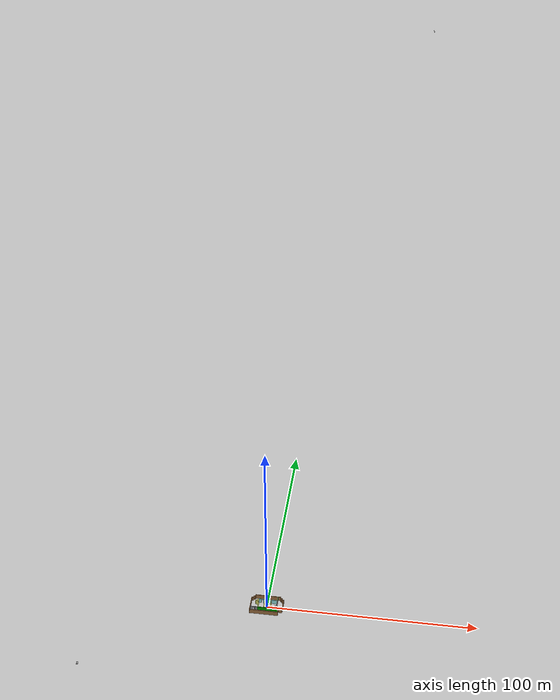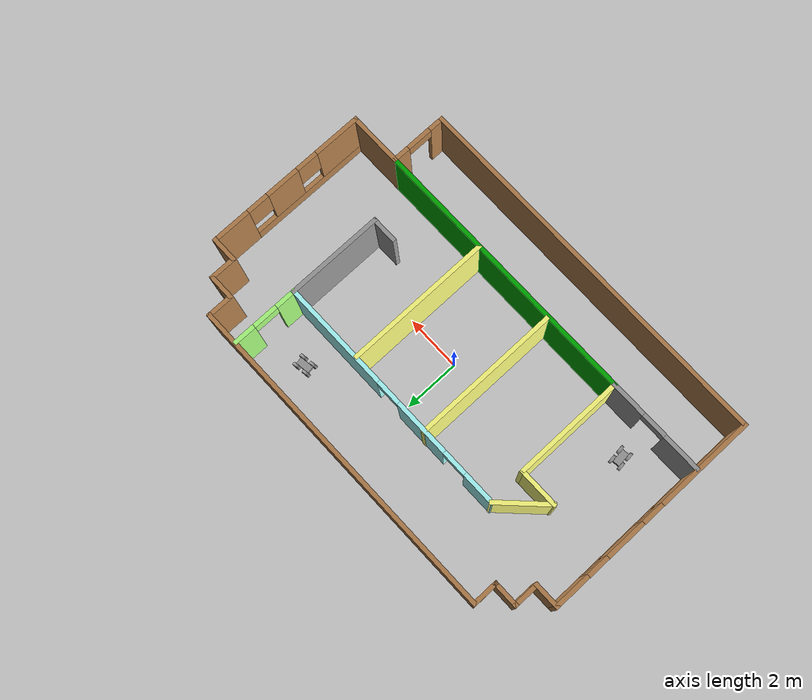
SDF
<sdf version="1.6">
 <world name="default">
  <plugin name="welcome" filename="libwelcome.so"/>
  <light name="sun" type="directional">
   <pose>0 0 10 0 -0 0</pose>
   <diffuse>0.8 0.8 0.8 1</diffuse>
   <specular>0.2 0.2 0.2 1</specular>
   <attenuation>
    <range>1000</range>
    <constant>0.9</constant>
    <linear>0.01</linear>
    <quadratic>0.001</quadratic>
   </attenuation>
   <direction>-0.5 0.1 -0.9</direction>
  </light>
  <gravity>0 0 -9.8</gravity>
  <magnetic_field>6e-06 2.3e-05 -4.2e-05</magnetic_field>
  <atmosphere type="adiabatic"/>
  <physics name="default_physics" default="0" type="ode">
   <max_step_size>0.001</max_step_size>
   <real_time_factor>1</real_time_factor>
   <real_time_update_rate>1000</real_time_update_rate>
  </physics>
  <scene><ambient>0.4 0.4 0.4 1</ambient><background>0.7 0.7 0.7 1</background><shadows>1</shadows></scene>
  <spherical_coordinates>
   <surface_model>EARTH_WGS84</surface_model>
   <latitude_deg>0</latitude_deg>
   <longitude_deg>0</longitude_deg>
   <elevation>0</elevation>
   <heading_deg>0</heading_deg>
  </spherical_coordinates>
  <model name="mybuilding">
   <pose>-0.05304 -0.01251 0 0 -0 0</pose>
   <link name="Wall_10">
    <collision name="Wall_10_Collision">
     <geometry><box><size>1 0.15 2.5</size></box></geometry>
     <pose>0 0 1.25 0 -0 0</pose>
    </collision>
    <visual name="Wall_10_Visual">
     <pose>0 0 1.25 0 -0 0</pose>
     <geometry><box><size>1 0.15 2.5</size></box></geometry>
     <material>
      <script><uri>file://media/materials/scripts/gazebo.material</uri><name>Gazebo/Wood</name></script>
      <ambient>1 1 1 1</ambient>
     </material>
     <meta><layer>0</layer></meta>
    </visual>
    <pose>-7.2 3.075 0 0 -0 3.14159</pose>
   </link>
   <link name="Wall_11">
    <pose>-7.625 -0.85 0 0 0 -1.5708</pose>
    <visual name="Wall_11_Visual_0">
     <pose>-3.31837 0 1.25 0 -0 0</pose>
     <geometry><box><size>1.36327 0.15 2.5</size></box></geometry>
     <material>
      <script><uri>file://media/materials/scripts/gazebo.material</uri><name>Gazebo/Wood</name></script>
      <ambient>1 1 1 1</ambient>
     </material>
     <meta><layer>0</layer></meta>
    </visual>
    <collision name="Wall_11_Collision_0">
     <geometry><box><size>1.36327 0.15 2.5</size></box></geometry>
     <pose>-3.31837 0 1.25 0 -0 0</pose>
    </collision>
    <visual name="Wall_11_Visual_1">
     <pose>0.681635 0 0.25 0 -0 0</pose>
     <geometry><box><size>6.63673 0.15 0.5</size></box></geometry>
     <material>
      <script><uri>file://media/materials/scripts/gazebo.material</uri><name>Gazebo/Wood</name></script>
      <ambient>1 1 1 1</ambient>
     </material>
     <meta><layer>0</layer></meta>
    </visual>
    <collision name="Wall_11_Collision_1">
     <geometry><box><size>6.63673 0.15 0.5</size></box></geometry>
     <pose>0.681635 0 0.25 0 -0 0</pose>
    </collision>
    <visual name="Wall_11_Visual_2">
     <pose>-1.09938 0 1.5 0 -0 0</pose>
     <geometry><box><size>1.4747 0.15 2</size></box></geometry>
     <material>
      <script><uri>file://media/materials/scripts/gazebo.material</uri><name>Gazebo/Wood</name></script>
      <ambient>1 1 1 1</ambient>
     </material>
     <meta><layer>0</layer></meta>
    </visual>
    <collision name="Wall_11_Collision_2">
     <geometry><box><size>1.4747 0.15 2</size></box></geometry>
     <pose>-1.09938 0 1.5 0 -0 0</pose>
    </collision>
    <visual name="Wall_11_Visual_3">
     <pose>2.21899 0 1.5 0 -0 0</pose>
     <geometry><box><size>3.56203 0.15 2</size></box></geometry>
     <material>
      <script><uri>file://media/materials/scripts/gazebo.material</uri><name>Gazebo/Wood</name></script>
      <ambient>1 1 1 1</ambient>
     </material>
     <meta><layer>0</layer></meta>
    </visual>
    <collision name="Wall_11_Collision_3">
     <geometry><box><size>3.56203 0.15 2</size></box></geometry>
     <pose>2.21899 0 1.5 0 -0 0</pose>
    </collision>
    <visual name="Wall_11_Visual_4">
     <pose>-2.23673 0 1.9 0 -0 0</pose>
     <geometry><box><size>0.8 0.15 1.2</size></box></geometry>
     <material>
      <script><uri>file://media/materials/scripts/gazebo.material</uri><name>Gazebo/Wood</name></script>
      <ambient>1 1 1 1</ambient>
     </material>
     <meta><layer>0</layer></meta>
    </visual>
    <collision name="Wall_11_Collision_4">
     <geometry><box><size>0.8 0.15 1.2</size></box></geometry>
     <pose>-2.23673 0 1.9 0 -0 0</pose>
    </collision>
    <visual name="Wall_11_Visual_5">
     <pose>0.037971 0 1.9 0 -0 0</pose>
     <geometry><box><size>0.8 0.15 1.2</size></box></geometry>
     <material>
      <script><uri>file://media/materials/scripts/gazebo.material</uri><name>Gazebo/Wood</name></script>
      <ambient>1 1 1 1</ambient>
     </material>
     <meta><layer>0</layer></meta>
    </visual>
    <collision name="Wall_11_Collision_5">
     <geometry><box><size>0.8 0.15 1.2</size></box></geometry>
     <pose>0.037971 0 1.9 0 -0 0</pose>
    </collision>
   </link>
   <link name="Wall_12">
    <collision name="Wall_12_Collision">
     <geometry><box><size>13.54 0.15 2.5</size></box></geometry>
     <pose>0 0 1.25 0 -0 0</pose>
    </collision>
    <visual name="Wall_12_Visual">
     <pose>0 0 1.25 0 -0 0</pose>
     <geometry><box><size>13.54 0.15 2.5</size></box></geometry>
     <material>
      <script><uri>file://media/materials/scripts/gazebo.material</uri><name>Gazebo/Wood</name></script>
      <ambient>1 1 1 1</ambient>
     </material>
     <meta><layer>0</layer></meta>
    </visual>
    <pose>-0.93 -4.775 0 0 -0 0</pose>
   </link>
   <link name="Wall_27">
    <collision name="Wall_27_Collision">
     <geometry><box><size>1 0.15 2.5</size></box></geometry>
     <pose>0 0 1.25 0 -0 0</pose>
    </collision>
    <visual name="Wall_27_Visual">
     <pose>0 0 1.25 0 -0 0</pose>
     <geometry><box><size>1 0.15 2.5</size></box></geometry>
     <material>
      <script><uri>file://media/materials/scripts/gazebo.material</uri><name>Gazebo/Wood</name></script>
      <ambient>1 1 1 1</ambient>
     </material>
     <meta><layer>0</layer></meta>
    </visual>
    <pose>-6.35 3.925 0 0 -0 0</pose>
   </link>
   <link name="Wall_28">
    <collision name="Wall_28_Collision">
     <geometry><box><size>1 0.15 2.5</size></box></geometry>
     <pose>0 0 1.25 0 -0 0</pose>
    </collision>
    <visual name="Wall_28_Visual">
     <pose>0 0 1.25 0 -0 0</pose>
     <geometry><box><size>1 0.15 2.5</size></box></geometry>
     <material>
      <script><uri>file://media/materials/scripts/gazebo.material</uri><name>Gazebo/Wood</name></script>
      <ambient>1 1 1 1</ambient>
     </material>
     <meta><layer>0</layer></meta>
    </visual>
    <pose>-5.925 4.35 0 0 -0 1.5708</pose>
   </link>
   <link name="Wall_29">
    <collision name="Wall_29_Collision">
     <geometry><box><size>12 0.15 2.5</size></box></geometry>
     <pose>0 0 1.25 0 -0 0</pose>
    </collision>
    <visual name="Wall_29_Visual">
     <pose>0 0 1.25 0 -0 0</pose>
     <geometry><box><size>12 0.15 2.5</size></box></geometry>
     <material>
      <script><uri>file://media/materials/scripts/gazebo.material</uri><name>Gazebo/Wood</name></script>
      <ambient>1 1 1 1</ambient>
     </material>
     <meta><layer>0</layer></meta>
    </visual>
    <pose>0 4.775 0 0 -0 0</pose>
   </link>
   <link name="Wall_3">
    <collision name="Wall_3_Collision">
     <geometry><box><size>1 0.15 2.5</size></box></geometry>
     <pose>0 0 1.25 0 -0 0</pose>
    </collision>
    <visual name="Wall_3_Visual">
     <pose>0 0 1.25 0 -0 0</pose>
     <geometry><box><size>1 0.15 2.5</size></box></geometry>
     <material>
      <script><uri>file://media/materials/scripts/gazebo.material</uri><name>Gazebo/Wood</name></script>
      <ambient>1 1 1 1</ambient>
     </material>
     <meta><layer>0</layer></meta>
    </visual>
    <pose>6.775 3.5 0 0 0 -1.5708</pose>
   </link>
   <link name="Wall_30">
    <collision name="Wall_30_Collision">
     <geometry><box><size>1 0.15 2.5</size></box></geometry>
     <pose>0 0 1.25 0 -0 0</pose>
    </collision>
    <visual name="Wall_30_Visual">
     <pose>0 0 1.25 0 -0 0</pose>
     <geometry><box><size>1 0.15 2.5</size></box></geometry>
     <material>
      <script><uri>file://media/materials/scripts/gazebo.material</uri><name>Gazebo/Wood</name></script>
      <ambient>1 1 1 1</ambient>
     </material>
     <meta><layer>0</layer></meta>
    </visual>
    <pose>5.925 4.35 0 0 0 -1.5708</pose>
   </link>
   <link name="Wall_31">
    <collision name="Wall_31_Collision">
     <geometry><box><size>1 0.15 2.5</size></box></geometry>
     <pose>0 0 1.25 0 -0 0</pose>
    </collision>
    <visual name="Wall_31_Visual">
     <pose>0 0 1.25 0 -0 0</pose>
     <geometry><box><size>1 0.15 2.5</size></box></geometry>
     <material>
      <script><uri>file://media/materials/scripts/gazebo.material</uri><name>Gazebo/Wood</name></script>
      <ambient>1 1 1 1</ambient>
     </material>
     <meta><layer>0</layer></meta>
    </visual>
    <pose>6.35 3.925 0 0 -0 0</pose>
   </link>
   <link name="Wall_33">
    <collision name="Wall_33_Collision">
     <geometry><box><size>2 0.15 2.5</size></box></geometry>
     <pose>0 0 1.25 0 -0 0</pose>
    </collision>
    <visual name="Wall_33_Visual">
     <pose>0 0 1.25 0 -0 0</pose>
     <geometry><box><size>2 0.15 2.5</size></box></geometry>
     <material>
      <script><uri>file://media/materials/scripts/gazebo.material</uri><name>Gazebo/Wood</name></script>
      <ambient>1 1 1 1</ambient>
     </material>
     <meta><layer>0</layer></meta>
    </visual>
    <pose>6.7 -2.775 0 0 -0 3.14159</pose>
   </link>
   <link name="Wall_34">
    <pose>5.775 -3.7 0 0 0 -1.5708</pose>
    <visual name="Wall_34_Visual_0">
     <pose>-0.676265 0 1.25 0 -0 0</pose>
     <geometry><box><size>0.64747 0.15 2.5</size></box></geometry>
     <material>
      <script><uri>file://media/materials/scripts/gazebo.material</uri><name>Gazebo/Wood</name></script>
      <ambient>1 1 1 1</ambient>
     </material>
     <meta><layer>0</layer></meta>
    </visual>
    <collision name="Wall_34_Collision_0">
     <geometry><box><size>0.64747 0.15 2.5</size></box></geometry>
     <pose>-0.676265 0 1.25 0 -0 0</pose>
    </collision>
    <visual name="Wall_34_Visual_1">
     <pose>0.773735 0 1.25 0 -0 0</pose>
     <geometry><box><size>0.45253 0.15 2.5</size></box></geometry>
     <material>
      <script><uri>file://media/materials/scripts/gazebo.material</uri><name>Gazebo/Wood</name></script>
      <ambient>1 1 1 1</ambient>
     </material>
     <meta><layer>0</layer></meta>
    </visual>
    <collision name="Wall_34_Collision_1">
     <geometry><box><size>0.45253 0.15 2.5</size></box></geometry>
     <pose>0.773735 0 1.25 0 -0 0</pose>
    </collision>
    <visual name="Wall_34_Visual_2">
     <pose>0.09747 0 2.25 0 -0 0</pose>
     <geometry><box><size>0.9 0.15 0.5</size></box></geometry>
     <material>
      <script><uri>file://media/materials/scripts/gazebo.material</uri><name>Gazebo/Wood</name></script>
      <ambient>1 1 1 1</ambient>
     </material>
     <meta><layer>0</layer></meta>
    </visual>
    <collision name="Wall_34_Collision_2">
     <geometry><box><size>0.9 0.15 0.5</size></box></geometry>
     <pose>0.09747 0 2.25 0 -0 0</pose>
    </collision>
   </link>
   <link name="Wall_36">
    <collision name="Wall_36_Collision">
     <geometry><box><size>10 0.15 2.5</size></box></geometry>
     <pose>0 0 1.25 0 -0 0</pose>
    </collision>
    <visual name="Wall_36_Visual">
     <pose>0 0 1.25 0 -0 0</pose>
     <geometry><box><size>10 0.15 2.5</size></box></geometry>
     <material>
      <script><uri>file://media/materials/scripts/gazebo.material</uri><name>Gazebo/Grey</name></script>
      <ambient>0 0.666667 0 1</ambient>
     </material>
     <meta><layer>0</layer></meta>
    </visual>
    <pose>0.85 -2.775 0 0 -0 3.14159</pose>
   </link>
   <link name="Wall_37">
    <collision name="Wall_37_Collision">
     <geometry><box><size>4 0.15 2.5</size></box></geometry>
     <pose>0 0 1.25 0 -0 0</pose>
    </collision>
    <visual name="Wall_37_Visual">
     <pose>0 0 1.25 0 -0 0</pose>
     <geometry><box><size>4 0.15 2.5</size></box></geometry>
     <material>
      <script><uri>file://media/materials/scripts/gazebo.material</uri><name>Gazebo/Grey</name></script>
      <ambient>1 1 0.498039 1</ambient>
     </material>
     <meta><layer>0</layer></meta>
    </visual>
    <pose>-4.075 -0.85 0 0 -0 1.5708</pose>
   </link>
   <link name="Wall_39">
    <pose>-5.82 -2.775 0 0 -0 3.14159</pose>
    <visual name="Wall_39_Visual_0">
     <pose>-1.16071 0 1.25 0 -0 0</pose>
     <geometry><box><size>1.31859 0.15 2.5</size></box></geometry>
     <material>
      <script><uri>file://media/materials/scripts/gazebo.material</uri><name>Gazebo/Grey</name></script>
      <ambient>1 1 1 1</ambient>
     </material>
     <meta><layer>0</layer></meta>
    </visual>
    <collision name="Wall_39_Collision_0">
     <geometry><box><size>1.31859 0.15 2.5</size></box></geometry>
     <pose>-1.16071 0 1.25 0 -0 0</pose>
    </collision>
    <visual name="Wall_39_Visual_1">
     <pose>1.10929 0 1.25 0 -0 0</pose>
     <geometry><box><size>1.42141 0.15 2.5</size></box></geometry>
     <material>
      <script><uri>file://media/materials/scripts/gazebo.material</uri><name>Gazebo/Grey</name></script>
      <ambient>1 1 1 1</ambient>
     </material>
     <meta><layer>0</layer></meta>
    </visual>
    <collision name="Wall_39_Collision_1">
     <geometry><box><size>1.42141 0.15 2.5</size></box></geometry>
     <pose>1.10929 0 1.25 0 -0 0</pose>
    </collision>
    <visual name="Wall_39_Visual_2">
     <pose>-0.051413 0 2.25 0 -0 0</pose>
     <geometry><box><size>0.9 0.15 0.5</size></box></geometry>
     <material>
      <script><uri>file://media/materials/scripts/gazebo.material</uri><name>Gazebo/Grey</name></script>
      <ambient>1 1 1 1</ambient>
     </material>
     <meta><layer>0</layer></meta>
    </visual>
    <collision name="Wall_39_Collision_2">
     <geometry><box><size>0.9 0.15 0.5</size></box></geometry>
     <pose>-0.051413 0 2.25 0 -0 0</pose>
    </collision>
   </link>
   <link name="Wall_4">
    <collision name="Wall_4_Collision">
     <geometry><box><size>1 0.15 2.5</size></box></geometry>
     <pose>0 0 1.25 0 -0 0</pose>
    </collision>
    <visual name="Wall_4_Visual">
     <pose>0 0 1.25 0 -0 0</pose>
     <geometry><box><size>1 0.15 2.5</size></box></geometry>
     <material>
      <script><uri>file://media/materials/scripts/gazebo.material</uri><name>Gazebo/Wood</name></script>
      <ambient>1 1 1 1</ambient>
     </material>
     <meta><layer>0</layer></meta>
    </visual>
    <pose>7.2 3.075 0 0 -0 0</pose>
   </link>
   <link name="Wall_41">
    <collision name="Wall_41_Collision">
     <geometry><box><size>1.5 0.15 2.5</size></box></geometry>
     <pose>0 0 1.25 0 -0 0</pose>
    </collision>
    <visual name="Wall_41_Visual">
     <pose>0 0 1.25 0 -0 0</pose>
     <geometry><box><size>1.5 0.15 2.5</size></box></geometry>
     <material>
      <script><uri>file://media/materials/scripts/gazebo.material</uri><name>Gazebo/Grey</name></script>
      <ambient>1 1 0.498039 1</ambient>
     </material>
     <meta><layer>0</layer></meta>
    </visual>
    <pose>-4.75 1.075 0 0 -0 3.14159</pose>
   </link>
   <link name="Wall_42">
    <collision name="Wall_42_Collision">
     <geometry><box><size>2 0.15 2.5</size></box></geometry>
     <pose>0 0 1.25 0 -0 0</pose>
    </collision>
    <visual name="Wall_42_Visual">
     <pose>0 0 1.25 0 -0 0</pose>
     <geometry><box><size>2 0.15 2.5</size></box></geometry>
     <material>
      <script><uri>file://media/materials/scripts/gazebo.material</uri><name>Gazebo/Grey</name></script>
      <ambient>1 1 0.498039 1</ambient>
     </material>
     <meta><layer>0</layer></meta>
    </visual>
    <pose>-4.77093 1.72907 0 0 -0 0.785398</pose>
   </link>
   <link name="Wall_43">
    <pose>0.308147 2.38315 0 0 -0 0</pose>
    <visual name="Wall_43_Visual_0">
     <pose>-3.88669 0 1.25 0 -0 0</pose>
     <geometry><box><size>1.22662 0.15 2.5</size></box></geometry>
     <material>
      <script><uri>file://media/materials/scripts/gazebo.material</uri><name>Gazebo/Grey</name></script>
      <ambient>0.666667 1 1 1</ambient>
     </material>
     <meta><layer>0</layer></meta>
    </visual>
    <collision name="Wall_43_Collision_0">
     <geometry><box><size>1.22662 0.15 2.5</size></box></geometry>
     <pose>-3.88669 0 1.25 0 -0 0</pose>
    </collision>
    <visual name="Wall_43_Visual_1">
     <pose>-1.35541 0 1.25 0 -0 0</pose>
     <geometry><box><size>2.03595 0.15 2.5</size></box></geometry>
     <material>
      <script><uri>file://media/materials/scripts/gazebo.material</uri><name>Gazebo/Grey</name></script>
      <ambient>0.666667 1 1 1</ambient>
     </material>
     <meta><layer>0</layer></meta>
    </visual>
    <collision name="Wall_43_Collision_1">
     <geometry><box><size>2.03595 0.15 2.5</size></box></geometry>
     <pose>-1.35541 0 1.25 0 -0 0</pose>
    </collision>
    <visual name="Wall_43_Visual_2">
     <pose>2.53128 0 1.25 0 -0 0</pose>
     <geometry><box><size>3.93743 0.15 2.5</size></box></geometry>
     <material>
      <script><uri>file://media/materials/scripts/gazebo.material</uri><name>Gazebo/Grey</name></script>
      <ambient>0.666667 1 1 1</ambient>
     </material>
     <meta><layer>0</layer></meta>
    </visual>
    <collision name="Wall_43_Collision_2">
     <geometry><box><size>3.93743 0.15 2.5</size></box></geometry>
     <pose>2.53128 0 1.25 0 -0 0</pose>
    </collision>
    <visual name="Wall_43_Visual_3">
     <pose>-2.82338 0 2.25 0 -0 0</pose>
     <geometry><box><size>0.9 0.15 0.5</size></box></geometry>
     <material>
      <script><uri>file://media/materials/scripts/gazebo.material</uri><name>Gazebo/Grey</name></script>
      <ambient>0.666667 1 1 1</ambient>
     </material>
     <meta><layer>0</layer></meta>
    </visual>
    <collision name="Wall_43_Collision_3">
     <geometry><box><size>0.9 0.15 0.5</size></box></geometry>
     <pose>-2.82338 0 2.25 0 -0 0</pose>
    </collision>
    <visual name="Wall_43_Visual_4">
     <pose>0.112566 0 2.25 0 -0 0</pose>
     <geometry><box><size>0.9 0.15 0.5</size></box></geometry>
     <material>
      <script><uri>file://media/materials/scripts/gazebo.material</uri><name>Gazebo/Grey</name></script>
      <ambient>0.666667 1 1 1</ambient>
     </material>
     <meta><layer>0</layer></meta>
    </visual>
    <collision name="Wall_43_Collision_4">
     <geometry><box><size>0.9 0.15 0.5</size></box></geometry>
     <pose>0.112566 0 2.25 0 -0 0</pose>
    </collision>
   </link>
   <link name="Wall_44">
    <pose>4.73315 3.55815 0 0 -0 1.5708</pose>
    <visual name="Wall_44_Visual_0">
     <pose>-0.851259 0 1.25 0 -0 0</pose>
     <geometry><box><size>0.797482 0.15 2.5</size></box></geometry>
     <material>
      <script><uri>file://media/materials/scripts/gazebo.material</uri><name>Gazebo/Grey</name></script>
      <ambient>0.666667 1 0.498039 1</ambient>
     </material>
     <meta><layer>0</layer></meta>
    </visual>
    <collision name="Wall_44_Collision_0">
     <geometry><box><size>0.797482 0.15 2.5</size></box></geometry>
     <pose>-0.851259 0 1.25 0 -0 0</pose>
    </collision>
    <visual name="Wall_44_Visual_1">
     <pose>0.848741 0 1.25 0 -0 0</pose>
     <geometry><box><size>0.802518 0.15 2.5</size></box></geometry>
     <material>
      <script><uri>file://media/materials/scripts/gazebo.material</uri><name>Gazebo/Grey</name></script>
      <ambient>0.666667 1 0.498039 1</ambient>
     </material>
     <meta><layer>0</layer></meta>
    </visual>
    <collision name="Wall_44_Collision_1">
     <geometry><box><size>0.802518 0.15 2.5</size></box></geometry>
     <pose>0.848741 0 1.25 0 -0 0</pose>
    </collision>
    <visual name="Wall_44_Visual_2">
     <pose>-0.002518 0 2.25 0 -0 0</pose>
     <geometry><box><size>0.9 0.15 0.5</size></box></geometry>
     <material>
      <script><uri>file://media/materials/scripts/gazebo.material</uri><name>Gazebo/Grey</name></script>
      <ambient>0.666667 1 0.498039 1</ambient>
     </material>
     <meta><layer>0</layer></meta>
    </visual>
    <collision name="Wall_44_Collision_2">
     <geometry><box><size>0.9 0.15 0.5</size></box></geometry>
     <pose>-0.002518 0 2.25 0 -0 0</pose>
    </collision>
   </link>
   <link name="Wall_46">
    <collision name="Wall_46_Collision">
     <geometry><box><size>5.25 0.15 2.5</size></box></geometry>
     <pose>0 0 1.25 0 -0 0</pose>
    </collision>
    <visual name="Wall_46_Visual">
     <pose>0 0 1.25 0 -0 0</pose>
     <geometry><box><size>5.25 0.15 2.5</size></box></geometry>
     <material>
      <script><uri>file://media/materials/scripts/gazebo.material</uri><name>Gazebo/Grey</name></script>
      <ambient>1 1 0.498039 1</ambient>
     </material>
     <meta><layer>0</layer></meta>
    </visual>
    <pose>-1.18669 -0.145072 0 0 0 -1.5708</pose>
   </link>
   <link name="Wall_48">
    <collision name="Wall_48_Collision">
     <geometry><box><size>5.25 0.15 2.5</size></box></geometry>
     <pose>0 0 1.25 0 -0 0</pose>
    </collision>
    <visual name="Wall_48_Visual">
     <pose>0 0 1.25 0 -0 0</pose>
     <geometry><box><size>5.25 0.15 2.5</size></box></geometry>
     <material>
      <script><uri>file://media/materials/scripts/gazebo.material</uri><name>Gazebo/Grey</name></script>
      <ambient>1 1 0.498039 1</ambient>
     </material>
     <meta><layer>0</layer></meta>
    </visual>
    <pose>1.89331 -0.205072 0 0 0 -1.5708</pose>
   </link>
   <link name="Wall_5">
    <pose>7.625 0.15 0 0 0 -1.5708</pose>
    <visual name="Wall_5_Visual_0">
     <pose>-2.29191 0 1.25 0 -0 0</pose>
     <geometry><box><size>1.41617 0.15 2.5</size></box></geometry>
     <material>
      <script><uri>file://media/materials/scripts/gazebo.material</uri><name>Gazebo/Wood</name></script>
      <ambient>1 1 1 1</ambient>
     </material>
     <meta><layer>0</layer></meta>
    </visual>
    <collision name="Wall_5_Collision_0">
     <geometry><box><size>1.41617 0.15 2.5</size></box></geometry>
     <pose>-2.29191 0 1.25 0 -0 0</pose>
    </collision>
    <visual name="Wall_5_Visual_1">
     <pose>0.708086 0 0.25 0 -0 0</pose>
     <geometry><box><size>4.58383 0.15 0.5</size></box></geometry>
     <material>
      <script><uri>file://media/materials/scripts/gazebo.material</uri><name>Gazebo/Wood</name></script>
      <ambient>1 1 1 1</ambient>
     </material>
     <meta><layer>0</layer></meta>
    </visual>
    <collision name="Wall_5_Collision_1">
     <geometry><box><size>4.58383 0.15 0.5</size></box></geometry>
     <pose>0.708086 0 0.25 0 -0 0</pose>
    </collision>
    <visual name="Wall_5_Visual_2">
     <pose>-0.165504 0 1.5 0 -0 0</pose>
     <geometry><box><size>1.23665 0.15 2</size></box></geometry>
     <material>
      <script><uri>file://media/materials/scripts/gazebo.material</uri><name>Gazebo/Wood</name></script>
      <ambient>1 1 1 1</ambient>
     </material>
     <meta><layer>0</layer></meta>
    </visual>
    <collision name="Wall_5_Collision_2">
     <geometry><box><size>1.23665 0.15 2</size></box></geometry>
     <pose>-0.165504 0 1.5 0 -0 0</pose>
    </collision>
    <visual name="Wall_5_Visual_3">
     <pose>2.12641 0 1.5 0 -0 0</pose>
     <geometry><box><size>1.74718 0.15 2</size></box></geometry>
     <material>
      <script><uri>file://media/materials/scripts/gazebo.material</uri><name>Gazebo/Wood</name></script>
      <ambient>1 1 1 1</ambient>
     </material>
     <meta><layer>0</layer></meta>
    </visual>
    <collision name="Wall_5_Collision_3">
     <geometry><box><size>1.74718 0.15 2</size></box></geometry>
     <pose>2.12641 0 1.5 0 -0 0</pose>
    </collision>
    <visual name="Wall_5_Visual_4">
     <pose>-1.18383 0 1.9 0 -0 0</pose>
     <geometry><box><size>0.8 0.15 1.2</size></box></geometry>
     <material>
      <script><uri>file://media/materials/scripts/gazebo.material</uri><name>Gazebo/Wood</name></script>
      <ambient>1 1 1 1</ambient>
     </material>
     <meta><layer>0</layer></meta>
    </visual>
    <collision name="Wall_5_Collision_4">
     <geometry><box><size>0.8 0.15 1.2</size></box></geometry>
     <pose>-1.18383 0 1.9 0 -0 0</pose>
    </collision>
    <visual name="Wall_5_Visual_5">
     <pose>0.852821 0 1.9 0 -0 0</pose>
     <geometry><box><size>0.8 0.15 1.2</size></box></geometry>
     <material>
      <script><uri>file://media/materials/scripts/gazebo.material</uri><name>Gazebo/Wood</name></script>
      <ambient>1 1 1 1</ambient>
     </material>
     <meta><layer>0</layer></meta>
    </visual>
    <collision name="Wall_5_Collision_5">
     <geometry><box><size>0.8 0.15 1.2</size></box></geometry>
     <pose>0.852821 0 1.9 0 -0 0</pose>
    </collision>
   </link>
   <link name="Wall_50">
    <collision name="Wall_50_Collision">
     <geometry><box><size>3.5 0.15 2.5</size></box></geometry>
     <pose>0 0 1.25 0 -0 0</pose>
    </collision>
    <visual name="Wall_50_Visual">
     <pose>0 0 1.25 0 -0 0</pose>
     <geometry><box><size>3.5 0.15 2.5</size></box></geometry>
     <material>
      <script><uri>file://media/materials/scripts/gazebo.material</uri><name>Gazebo/Grey</name></script>
      <ambient>0 0 0 1</ambient>
     </material>
     <meta><layer>0</layer></meta>
    </visual>
    <pose>4.73315 0.708147 0 0 0 -1.5708</pose>
   </link>
   <link name="Wall_51">
    <collision name="Wall_51_Collision">
     <geometry><box><size>1 0.15 2.5</size></box></geometry>
     <pose>0 0 1.25 0 -0 0</pose>
    </collision>
    <visual name="Wall_51_Visual">
     <pose>0 0 1.25 0 -0 0</pose>
     <geometry><box><size>1 0.15 2.5</size></box></geometry>
     <material>
      <script><uri>file://media/materials/scripts/gazebo.material</uri><name>Gazebo/Grey</name></script>
      <ambient>0 0 0 1</ambient>
     </material>
     <meta><layer>0</layer></meta>
    </visual>
    <pose>4.30815 -0.966853 0 0 -0 3.14159</pose>
   </link>
   <link name="Wall_9">
    <collision name="Wall_9_Collision">
     <geometry><box><size>1 0.15 2.5</size></box></geometry>
     <pose>0 0 1.25 0 -0 0</pose>
    </collision>
    <visual name="Wall_9_Visual">
     <pose>0 0 1.25 0 -0 0</pose>
     <geometry><box><size>1 0.15 2.5</size></box></geometry>
     <material>
      <script><uri>file://media/materials/scripts/gazebo.material</uri><name>Gazebo/Wood</name></script>
      <ambient>1 1 1 1</ambient>
     </material>
     <meta><layer>0</layer></meta>
    </visual>
    <pose>-6.775 3.5 0 0 0 -1.5708</pose>
   </link>
   <static>1</static>
  </model>
  <model name="robot">
   <link name="link_0">
    <inertial>
     <mass>1</mass>
     <inertia>
      <ixx>0.166667</ixx>
      <ixy>0</ixy>
      <ixz>0</ixz>
      <iyy>0.166667</iyy>
      <iyz>0</iyz>
      <izz>0.166667</izz>
     </inertia>
    </inertial>
    <visual name="visual">
     <geometry><box><size>0.3 1 0.1</size></box></geometry>
     <material>
      <lighting>1</lighting>
      <script><uri>file://media/materials/scripts/gazebo.material</uri><name>Gazebo/Grey</name></script>
      <ambient>0.3 0.3 0.3 1</ambient>
      <diffuse>0.7 0.7 0.7 1</diffuse>
      <specular>0.01 0.01 0.01 1</specular>
      <emissive>0 0 0 1</emissive>
      <shader type="vertex"><normal_map>__default__</normal_map></shader>
     </material>
    </visual>
    <collision name="collision">
     <geometry><box><size>0.3 1 0.1</size></box></geometry>
     <surface>
      <friction>
       <ode><mu>1</mu><mu2>1</mu2><fdir1>0 0 0</fdir1><slip1>0</slip1><slip2>0</slip2></ode>
       <torsional>
        <coefficient>1</coefficient>
        <patch_radius>0</patch_radius>
        <surface_radius>0</surface_radius>
        <use_patch_radius>1</use_patch_radius>
        <ode><slip>0</slip></ode>
       </torsional>
      </friction>
      <bounce><restitution_coefficient>0</restitution_coefficient><threshold>1e+06</threshold></bounce>
      <contact>
       <collide_without_contact>0</collide_without_contact>
       <collide_without_contact_bitmask>1</collide_without_contact_bitmask>
       <collide_bitmask>1</collide_bitmask>
       <ode>
        <soft_cfm>0</soft_cfm>
        <soft_erp>0.2</soft_erp>
        <kp>1e+13</kp>
        <kd>1</kd>
        <max_vel>0.01</max_vel>
        <min_depth>0</min_depth>
       </ode>
       <bullet>
        <split_impulse>1</split_impulse>
        <split_impulse_penetration_threshold>-0.01</split_impulse_penetration_threshold>
        <soft_cfm>0</soft_cfm>
        <soft_erp>0.2</soft_erp>
        <kp>1e+13</kp>
        <kd>1</kd>
       </bullet>
      </contact>
     </surface>
    </collision>
   </link>
   <link name="link_1">
    <pose>0 -0.550019 0 1.5707 -0 0</pose>
    <inertial>
     <mass>1</mass>
     <inertia><ixx>0.145833</ixx><ixy>0</ixy><ixz>0</ixz><iyy>0.145833</iyy><iyz>0</iyz><izz>0.125</izz></inertia>
    </inertial>
    <visual name="visual">
     <geometry><cylinder><radius>0.2</radius><length>0.1</length></cylinder></geometry>
     <material>
      <lighting>1</lighting>
      <script><uri>file://media/materials/scripts/gazebo.material</uri><name>Gazebo/Grey</name></script>
      <ambient>0.3 0.3 0.3 1</ambient>
      <diffuse>0.7 0.7 0.7 1</diffuse>
      <specular>0.01 0.01 0.01 1</specular>
      <emissive>0 0 0 1</emissive>
      <shader type="vertex"><normal_map>__default__</normal_map></shader>
     </material>
    </visual>
    <collision name="collision">
     <geometry><cylinder><radius>0.2</radius><length>0.1</length></cylinder></geometry>
     <surface>
      <friction>
       <ode><mu>1</mu><mu2>1</mu2><fdir1>0 0 0</fdir1><slip1>0</slip1><slip2>0</slip2></ode>
       <torsional>
        <coefficient>1</coefficient>
        <patch_radius>0</patch_radius>
        <surface_radius>0</surface_radius>
        <use_patch_radius>1</use_patch_radius>
        <ode><slip>0</slip></ode>
       </torsional>
      </friction>
      <bounce><restitution_coefficient>0</restitution_coefficient><threshold>1e+06</threshold></bounce>
      <contact>
       <collide_without_contact>0</collide_without_contact>
       <collide_without_contact_bitmask>1</collide_without_contact_bitmask>
       <collide_bitmask>1</collide_bitmask>
       <ode>
        <soft_cfm>0</soft_cfm>
        <soft_erp>0.2</soft_erp>
        <kp>1e+13</kp>
        <kd>1</kd>
        <max_vel>0.01</max_vel>
        <min_depth>0</min_depth>
       </ode>
       <bullet>
        <split_impulse>1</split_impulse>
        <split_impulse_penetration_threshold>-0.01</split_impulse_penetration_threshold>
        <soft_cfm>0</soft_cfm>
        <soft_erp>0.2</soft_erp>
        <kp>1e+13</kp>
        <kd>1</kd>
       </bullet>
      </contact>
     </surface>
    </collision>
   </link>
   <link name="link_1_clone">
    <pose>0 0.550019 0 1.5707 -0 0</pose>
    <inertial>
     <mass>1</mass>
     <inertia><ixx>0.145833</ixx><ixy>0</ixy><ixz>0</ixz><iyy>0.145833</iyy><iyz>0</iyz><izz>0.125</izz></inertia>
    </inertial>
    <visual name="visual">
     <geometry><cylinder><radius>0.2</radius><length>0.1</length></cylinder></geometry>
     <material>
      <lighting>1</lighting>
      <script><uri>file://media/materials/scripts/gazebo.material</uri><name>Gazebo/Grey</name></script>
      <ambient>0.3 0.3 0.3 1</ambient>
      <diffuse>0.7 0.7 0.7 1</diffuse>
      <specular>0.01 0.01 0.01 1</specular>
      <emissive>0 0 0 1</emissive>
      <shader type="vertex"><normal_map>__default__</normal_map></shader>
     </material>
    </visual>
    <collision name="collision">
     <geometry><cylinder><radius>0.2</radius><length>0.1</length></cylinder></geometry>
     <surface>
      <friction>
       <ode><mu>1</mu><mu2>1</mu2><fdir1>0 0 0</fdir1><slip1>0</slip1><slip2>0</slip2></ode>
       <torsional>
        <coefficient>1</coefficient>
        <patch_radius>0</patch_radius>
        <surface_radius>0</surface_radius>
        <use_patch_radius>1</use_patch_radius>
        <ode><slip>0</slip></ode>
       </torsional>
      </friction>
      <bounce><restitution_coefficient>0</restitution_coefficient><threshold>1e+06</threshold></bounce>
      <contact>
       <collide_without_contact>0</collide_without_contact>
       <collide_without_contact_bitmask>1</collide_without_contact_bitmask>
       <collide_bitmask>1</collide_bitmask>
       <ode>
        <soft_cfm>0</soft_cfm>
        <soft_erp>0.2</soft_erp>
        <kp>1e+13</kp>
        <kd>1</kd>
        <max_vel>0.01</max_vel>
        <min_depth>0</min_depth>
       </ode>
       <bullet>
        <split_impulse>1</split_impulse>
        <split_impulse_penetration_threshold>-0.01</split_impulse_penetration_threshold>
        <soft_cfm>0</soft_cfm>
        <soft_erp>0.2</soft_erp>
        <kp>1e+13</kp>
        <kd>1</kd>
       </bullet>
      </contact>
     </surface>
    </collision>
   </link>
   <joint name="link_0_JOINT_1" type="revolute">
    <parent>link_0</parent>
    <child>link_1</child>
    <axis>
     <xyz>0 0 1</xyz>
     <use_parent_model_frame>0</use_parent_model_frame>
     <limit>
      <lower>-1.79769e+308</lower>
      <upper>1.79769e+308</upper>
      <effort>-1</effort>
      <velocity>-1</velocity>
     </limit>
     <dynamics>
      <spring_reference>0</spring_reference>
      <spring_stiffness>0</spring_stiffness>
      <damping>0</damping>
     </dynamics>
    </axis>
    <physics>
     <ode><limit><cfm>0</cfm><erp>0.2</erp></limit><suspension><cfm>0</cfm><erp>0.2</erp></suspension></ode>
    </physics>
   </joint>
   <joint name="link_0_JOINT_2" type="revolute">
    <parent>link_0</parent>
    <child>link_1_clone</child>
    <axis>
     <xyz>0 0 1</xyz>
     <use_parent_model_frame>0</use_parent_model_frame>
     <limit>
      <lower>-1.79769e+308</lower>
      <upper>1.79769e+308</upper>
      <effort>-1</effort>
      <velocity>-1</velocity>
     </limit>
     <dynamics>
      <spring_reference>0</spring_reference>
      <spring_stiffness>0</spring_stiffness>
      <damping>0</damping>
     </dynamics>
    </axis>
    <physics>
     <ode><limit><cfm>0</cfm><erp>0.2</erp></limit><suspension><cfm>0</cfm><erp>0.2</erp></suspension></ode>
    </physics>
   </joint>
   <static>0</static>
   <pose>31.9941 482.89 0.612799 -1.80532 -0.52642 -0.588105</pose>
  </model>
  <model name="4wheel">
   <link name="link_0">
    <inertial>
     <mass>1</mass>
     <inertia>
      <ixx>0.166667</ixx>
      <ixy>0</ixy>
      <ixz>0</ixz>
      <iyy>0.166667</iyy>
      <iyz>0</iyz>
      <izz>0.166667</izz>
     </inertia>
    </inertial>
    <visual name="visual">
     <geometry><box><size>0.7 1.5 0.3</size></box></geometry>
     <material>
      <lighting>1</lighting>
      <script><uri>file://media/materials/scripts/gazebo.material</uri><name>Gazebo/Grey</name></script>
      <ambient>0.3 0.3 0.3 1</ambient>
      <diffuse>0.7 0.7 0.7 1</diffuse>
      <specular>0.01 0.01 0.01 1</specular>
      <emissive>0 0 0 1</emissive>
      <shader type="vertex"><normal_map>__default__</normal_map></shader>
     </material>
    </visual>
    <collision name="collision">
     <geometry><box><size>0.7 1.5 0.3</size></box></geometry>
     <surface>
      <friction>
       <ode><mu>1</mu><mu2>1</mu2><fdir1>0 0 0</fdir1><slip1>0</slip1><slip2>0</slip2></ode>
       <torsional>
        <coefficient>1</coefficient>
        <patch_radius>0</patch_radius>
        <surface_radius>0</surface_radius>
        <use_patch_radius>1</use_patch_radius>
        <ode><slip>0</slip></ode>
       </torsional>
      </friction>
      <bounce><restitution_coefficient>0</restitution_coefficient><threshold>1e+06</threshold></bounce>
      <contact>
       <collide_without_contact>0</collide_without_contact>
       <collide_without_contact_bitmask>1</collide_without_contact_bitmask>
       <collide_bitmask>1</collide_bitmask>
       <ode>
        <soft_cfm>0</soft_cfm>
        <soft_erp>0.2</soft_erp>
        <kp>1e+13</kp>
        <kd>1</kd>
        <max_vel>0.01</max_vel>
        <min_depth>0</min_depth>
       </ode>
       <bullet>
        <split_impulse>1</split_impulse>
        <split_impulse_penetration_threshold>-0.01</split_impulse_penetration_threshold>
        <soft_cfm>0</soft_cfm>
        <soft_erp>0.2</soft_erp>
        <kp>1e+13</kp>
        <kd>1</kd>
       </bullet>
      </contact>
     </surface>
    </collision>
   </link>
   <link name="link_1">
    <pose>-0.400014 -0.6 0 0 1.5707 0</pose>
    <inertial>
     <mass>1</mass>
     <inertia><ixx>0.145833</ixx><ixy>0</ixy><ixz>0</ixz><iyy>0.145833</iyy><iyz>0</iyz><izz>0.125</izz></inertia>
    </inertial>
    <visual name="visual">
     <geometry><cylinder><radius>0.15</radius><length>0.1</length></cylinder></geometry>
     <material>
      <lighting>1</lighting>
      <script><uri>file://media/materials/scripts/gazebo.material</uri><name>Gazebo/Grey</name></script>
      <ambient>0.3 0.3 0.3 1</ambient>
      <diffuse>0.7 0.7 0.7 1</diffuse>
      <specular>0.01 0.01 0.01 1</specular>
      <emissive>0 0 0 1</emissive>
      <shader type="vertex"><normal_map>__default__</normal_map></shader>
     </material>
    </visual>
    <collision name="collision">
     <geometry><cylinder><radius>0.15</radius><length>0.1</length></cylinder></geometry>
     <surface>
      <friction>
       <ode><mu>1</mu><mu2>1</mu2><fdir1>0 0 0</fdir1><slip1>0</slip1><slip2>0</slip2></ode>
       <torsional>
        <coefficient>1</coefficient>
        <patch_radius>0</patch_radius>
        <surface_radius>0</surface_radius>
        <use_patch_radius>1</use_patch_radius>
        <ode><slip>0</slip></ode>
       </torsional>
      </friction>
      <bounce><restitution_coefficient>0</restitution_coefficient><threshold>1e+06</threshold></bounce>
      <contact>
       <collide_without_contact>0</collide_without_contact>
       <collide_without_contact_bitmask>1</collide_without_contact_bitmask>
       <collide_bitmask>1</collide_bitmask>
       <ode>
        <soft_cfm>0</soft_cfm>
        <soft_erp>0.2</soft_erp>
        <kp>1e+13</kp>
        <kd>1</kd>
        <max_vel>0.01</max_vel>
        <min_depth>0</min_depth>
       </ode>
       <bullet>
        <split_impulse>1</split_impulse>
        <split_impulse_penetration_threshold>-0.01</split_impulse_penetration_threshold>
        <soft_cfm>0</soft_cfm>
        <soft_erp>0.2</soft_erp>
        <kp>1e+13</kp>
        <kd>1</kd>
       </bullet>
      </contact>
     </surface>
    </collision>
   </link>
   <link name="link_1_clone">
    <pose>-0.400014 0.6 0 0 1.5707 0</pose>
    <inertial>
     <mass>1</mass>
     <inertia><ixx>0.145833</ixx><ixy>0</ixy><ixz>0</ixz><iyy>0.145833</iyy><iyz>0</iyz><izz>0.125</izz></inertia>
    </inertial>
    <visual name="visual">
     <geometry><cylinder><radius>0.15</radius><length>0.1</length></cylinder></geometry>
     <material>
      <lighting>1</lighting>
      <script><uri>file://media/materials/scripts/gazebo.material</uri><name>Gazebo/Grey</name></script>
      <ambient>0.3 0.3 0.3 1</ambient>
      <diffuse>0.7 0.7 0.7 1</diffuse>
      <specular>0.01 0.01 0.01 1</specular>
      <emissive>0 0 0 1</emissive>
      <shader type="vertex"><normal_map>__default__</normal_map></shader>
     </material>
    </visual>
    <collision name="collision">
     <geometry><cylinder><radius>0.15</radius><length>0.1</length></cylinder></geometry>
     <surface>
      <friction>
       <ode><mu>1</mu><mu2>1</mu2><fdir1>0 0 0</fdir1><slip1>0</slip1><slip2>0</slip2></ode>
       <torsional>
        <coefficient>1</coefficient>
        <patch_radius>0</patch_radius>
        <surface_radius>0</surface_radius>
        <use_patch_radius>1</use_patch_radius>
        <ode><slip>0</slip></ode>
       </torsional>
      </friction>
      <bounce><restitution_coefficient>0</restitution_coefficient><threshold>1e+06</threshold></bounce>
      <contact>
       <collide_without_contact>0</collide_without_contact>
       <collide_without_contact_bitmask>1</collide_without_contact_bitmask>
       <collide_bitmask>1</collide_bitmask>
       <ode>
        <soft_cfm>0</soft_cfm>
        <soft_erp>0.2</soft_erp>
        <kp>1e+13</kp>
        <kd>1</kd>
        <max_vel>0.01</max_vel>
        <min_depth>0</min_depth>
       </ode>
       <bullet>
        <split_impulse>1</split_impulse>
        <split_impulse_penetration_threshold>-0.01</split_impulse_penetration_threshold>
        <soft_cfm>0</soft_cfm>
        <soft_erp>0.2</soft_erp>
        <kp>1e+13</kp>
        <kd>1</kd>
       </bullet>
      </contact>
     </surface>
    </collision>
   </link>
   <link name="link_1_clone_0">
    <pose>0.400014 0.6 0 0 1.5707 0</pose>
    <inertial>
     <mass>1</mass>
     <inertia><ixx>0.145833</ixx><ixy>0</ixy><ixz>0</ixz><iyy>0.145833</iyy><iyz>0</iyz><izz>0.125</izz></inertia>
    </inertial>
    <visual name="visual">
     <geometry><cylinder><radius>0.15</radius><length>0.1</length></cylinder></geometry>
     <material>
      <lighting>1</lighting>
      <script><uri>file://media/materials/scripts/gazebo.material</uri><name>Gazebo/Grey</name></script>
      <ambient>0.3 0.3 0.3 1</ambient>
      <diffuse>0.7 0.7 0.7 1</diffuse>
      <specular>0.01 0.01 0.01 1</specular>
      <emissive>0 0 0 1</emissive>
      <shader type="vertex"><normal_map>__default__</normal_map></shader>
     </material>
    </visual>
    <collision name="collision">
     <geometry><cylinder><radius>0.15</radius><length>0.1</length></cylinder></geometry>
     <surface>
      <friction>
       <ode><mu>1</mu><mu2>1</mu2><fdir1>0 0 0</fdir1><slip1>0</slip1><slip2>0</slip2></ode>
       <torsional>
        <coefficient>1</coefficient>
        <patch_radius>0</patch_radius>
        <surface_radius>0</surface_radius>
        <use_patch_radius>1</use_patch_radius>
        <ode><slip>0</slip></ode>
       </torsional>
      </friction>
      <bounce><restitution_coefficient>0</restitution_coefficient><threshold>1e+06</threshold></bounce>
      <contact>
       <collide_without_contact>0</collide_without_contact>
       <collide_without_contact_bitmask>1</collide_without_contact_bitmask>
       <collide_bitmask>1</collide_bitmask>
       <ode>
        <soft_cfm>0</soft_cfm>
        <soft_erp>0.2</soft_erp>
        <kp>1e+13</kp>
        <kd>1</kd>
        <max_vel>0.01</max_vel>
        <min_depth>0</min_depth>
       </ode>
       <bullet>
        <split_impulse>1</split_impulse>
        <split_impulse_penetration_threshold>-0.01</split_impulse_penetration_threshold>
        <soft_cfm>0</soft_cfm>
        <soft_erp>0.2</soft_erp>
        <kp>1e+13</kp>
        <kd>1</kd>
       </bullet>
      </contact>
     </surface>
    </collision>
   </link>
   <link name="link_1_clone_1">
    <pose>0.400014 -0.6 0 0 1.5707 0</pose>
    <inertial>
     <mass>1</mass>
     <inertia><ixx>0.145833</ixx><ixy>0</ixy><ixz>0</ixz><iyy>0.145833</iyy><iyz>0</iyz><izz>0.125</izz></inertia>
    </inertial>
    <visual name="visual">
     <geometry><cylinder><radius>0.15</radius><length>0.1</length></cylinder></geometry>
     <material>
      <lighting>1</lighting>
      <script><uri>file://media/materials/scripts/gazebo.material</uri><name>Gazebo/Grey</name></script>
      <ambient>0.3 0.3 0.3 1</ambient>
      <diffuse>0.7 0.7 0.7 1</diffuse>
      <specular>0.01 0.01 0.01 1</specular>
      <emissive>0 0 0 1</emissive>
      <shader type="vertex"><normal_map>__default__</normal_map></shader>
     </material>
    </visual>
    <collision name="collision">
     <geometry><cylinder><radius>0.15</radius><length>0.1</length></cylinder></geometry>
     <surface>
      <friction>
       <ode><mu>1</mu><mu2>1</mu2><fdir1>0 0 0</fdir1><slip1>0</slip1><slip2>0</slip2></ode>
       <torsional>
        <coefficient>1</coefficient>
        <patch_radius>0</patch_radius>
        <surface_radius>0</surface_radius>
        <use_patch_radius>1</use_patch_radius>
        <ode><slip>0</slip></ode>
       </torsional>
      </friction>
      <bounce><restitution_coefficient>0</restitution_coefficient><threshold>1e+06</threshold></bounce>
      <contact>
       <collide_without_contact>0</collide_without_contact>
       <collide_without_contact_bitmask>1</collide_without_contact_bitmask>
       <collide_bitmask>1</collide_bitmask>
       <ode>
        <soft_cfm>0</soft_cfm>
        <soft_erp>0.2</soft_erp>
        <kp>1e+13</kp>
        <kd>1</kd>
        <max_vel>0.01</max_vel>
        <min_depth>0</min_depth>
       </ode>
       <bullet>
        <split_impulse>1</split_impulse>
        <split_impulse_penetration_threshold>-0.01</split_impulse_penetration_threshold>
        <soft_cfm>0</soft_cfm>
        <soft_erp>0.2</soft_erp>
        <kp>1e+13</kp>
        <kd>1</kd>
       </bullet>
      </contact>
     </surface>
    </collision>
   </link>
   <joint name="link_0_JOINT_0" type="revolute">
    <parent>link_0</parent>
    <child>link_1_clone_1</child>
    <axis>
     <xyz>0 1 0</xyz>
     <use_parent_model_frame>0</use_parent_model_frame>
     <limit>
      <lower>-1.79769e+308</lower>
      <upper>1.79769e+308</upper>
      <effort>-1</effort>
      <velocity>-1</velocity>
     </limit>
     <dynamics>
      <spring_reference>0</spring_reference>
      <spring_stiffness>0</spring_stiffness>
      <damping>0</damping>
     </dynamics>
    </axis>
    <physics>
     <ode><limit><cfm>0</cfm><erp>0.2</erp></limit><suspension><cfm>0</cfm><erp>0.2</erp></suspension></ode>
    </physics>
   </joint>
   <joint name="link_0_JOINT_1" type="revolute">
    <parent>link_0</parent>
    <child>link_1_clone_0</child>
    <axis>
     <xyz>0 1 0</xyz>
     <use_parent_model_frame>0</use_parent_model_frame>
     <limit>
      <lower>-1.79769e+308</lower>
      <upper>1.79769e+308</upper>
      <effort>-1</effort>
      <velocity>-1</velocity>
     </limit>
     <dynamics>
      <spring_reference>0</spring_reference>
      <spring_stiffness>0</spring_stiffness>
      <damping>0</damping>
     </dynamics>
    </axis>
    <physics>
     <ode><limit><cfm>0</cfm><erp>0.2</erp></limit><suspension><cfm>0</cfm><erp>0.2</erp></suspension></ode>
    </physics>
   </joint>
   <joint name="link_0_JOINT_2" type="revolute">
    <parent>link_0</parent>
    <child>link_1_clone</child>
    <axis>
     <xyz>0 1 0</xyz>
     <use_parent_model_frame>0</use_parent_model_frame>
     <limit>
      <lower>-1.79769e+308</lower>
      <upper>1.79769e+308</upper>
      <effort>-1</effort>
      <velocity>-1</velocity>
     </limit>
     <dynamics>
      <spring_reference>0</spring_reference>
      <spring_stiffness>0</spring_stiffness>
      <damping>0</damping>
     </dynamics>
    </axis>
    <physics>
     <ode><limit><cfm>0</cfm><erp>0.2</erp></limit><suspension><cfm>0</cfm><erp>0.2</erp></suspension></ode>
    </physics>
   </joint>
   <joint name="link_0_JOINT_3" type="revolute">
    <parent>link_0</parent>
    <child>link_1</child>
    <axis>
     <xyz>0 0 1</xyz>
     <use_parent_model_frame>0</use_parent_model_frame>
     <limit>
      <lower>-1.79769e+308</lower>
      <upper>1.79769e+308</upper>
      <effort>-1</effort>
      <velocity>-1</velocity>
     </limit>
     <dynamics>
      <spring_reference>0</spring_reference>
      <spring_stiffness>0</spring_stiffness>
      <damping>0</damping>
     </dynamics>
    </axis>
    <physics>
     <ode><limit><cfm>0</cfm><erp>0.2</erp></limit><suspension><cfm>0</cfm><erp>0.2</erp></suspension></ode>
    </physics>
   </joint>
   <joint name="link_0_JOINT_4" type="revolute">
    <parent>link_0</parent>
    <child>link_1_clone_1</child>
    <axis>
     <xyz>0 0 1</xyz>
     <use_parent_model_frame>0</use_parent_model_frame>
     <limit>
      <lower>-1.79769e+308</lower>
      <upper>1.79769e+308</upper>
      <effort>-1</effort>
      <velocity>-1</velocity>
     </limit>
     <dynamics>
      <spring_reference>0</spring_reference>
      <spring_stiffness>0</spring_stiffness>
      <damping>0</damping>
     </dynamics>
    </axis>
    <physics>
     <ode><limit><cfm>0</cfm><erp>0.2</erp></limit><suspension><cfm>0</cfm><erp>0.2</erp></suspension></ode>
    </physics>
   </joint>
   <joint name="link_0_JOINT_5" type="revolute">
    <parent>link_0</parent>
    <child>link_1_clone_1</child>
    <axis>
     <xyz>0 0 1</xyz>
     <use_parent_model_frame>0</use_parent_model_frame>
     <limit>
      <lower>-1.79769e+308</lower>
      <upper>1.79769e+308</upper>
      <effort>-1</effort>
      <velocity>-1</velocity>
     </limit>
     <dynamics>
      <spring_reference>0</spring_reference>
      <spring_stiffness>0</spring_stiffness>
      <damping>0</damping>
     </dynamics>
    </axis>
    <physics>
     <ode><limit><cfm>0</cfm><erp>0.2</erp></limit><suspension><cfm>0</cfm><erp>0.2</erp></suspension></ode>
    </physics>
   </joint>
   <joint name="link_0_JOINT_6" type="revolute">
    <parent>link_0</parent>
    <child>link_1_clone_0</child>
    <axis>
     <xyz>0 0 1</xyz>
     <use_parent_model_frame>0</use_parent_model_frame>
     <limit>
      <lower>-1.79769e+308</lower>
      <upper>1.79769e+308</upper>
      <effort>-1</effort>
      <velocity>-1</velocity>
     </limit>
     <dynamics>
      <spring_reference>0</spring_reference>
      <spring_stiffness>0</spring_stiffness>
      <damping>0</damping>
     </dynamics>
    </axis>
    <physics>
     <ode><limit><cfm>0</cfm><erp>0.2</erp></limit><suspension><cfm>0</cfm><erp>0.2</erp></suspension></ode>
    </physics>
   </joint>
   <joint name="link_0_JOINT_7" type="revolute">
    <parent>link_0</parent>
    <child>link_1_clone</child>
    <axis>
     <xyz>0 0 1</xyz>
     <use_parent_model_frame>0</use_parent_model_frame>
     <limit>
      <lower>-1.79769e+308</lower>
      <upper>1.79769e+308</upper>
      <effort>-1</effort>
      <velocity>-1</velocity>
     </limit>
     <dynamics>
      <spring_reference>0</spring_reference>
      <spring_stiffness>0</spring_stiffness>
      <damping>0</damping>
     </dynamics>
    </axis>
    <physics>
     <ode><limit><cfm>0</cfm><erp>0.2</erp></limit><suspension><cfm>0</cfm><erp>0.2</erp></suspension></ode>
    </physics>
   </joint>
   <joint name="link_0_JOINT_8" type="revolute">
    <parent>link_0</parent>
    <child>link_1</child>
    <axis>
     <xyz>0 0 1</xyz>
     <use_parent_model_frame>0</use_parent_model_frame>
     <limit>
      <lower>-1.79769e+308</lower>
      <upper>1.79769e+308</upper>
      <effort>-1</effort>
      <velocity>-1</velocity>
     </limit>
     <dynamics>
      <spring_reference>0</spring_reference>
      <spring_stiffness>0</spring_stiffness>
      <damping>0</damping>
     </dynamics>
    </axis>
    <physics>
     <ode><limit><cfm>0</cfm><erp>0.2</erp></limit><suspension><cfm>0</cfm><erp>0.2</erp></suspension></ode>
    </physics>
   </joint>
   <joint name="link_0_JOINT_9" type="revolute">
    <parent>link_0</parent>
    <child>link_1</child>
    <axis>
     <xyz>0 0 1</xyz>
     <use_parent_model_frame>0</use_parent_model_frame>
     <limit>
      <lower>-1.79769e+308</lower>
      <upper>1.79769e+308</upper>
      <effort>-1</effort>
      <velocity>-1</velocity>
     </limit>
     <dynamics>
      <spring_reference>0</spring_reference>
      <spring_stiffness>0</spring_stiffness>
      <damping>0</damping>
     </dynamics>
    </axis>
    <physics>
     <ode><limit><cfm>0</cfm><erp>0.2</erp></limit><suspension><cfm>0</cfm><erp>0.2</erp></suspension></ode>
    </physics>
   </joint>
   <static>0</static>
   <pose>-81.9549 -46.5975 0.150003 4e-06 0 -2.99935</pose>
  </model>
  <model name="ground_plane">
   <static>1</static>
   <link name="link">
    <collision name="collision">
     <geometry><plane><normal>0 0 1</normal><size>100 100</size></plane></geometry>
     <surface><friction><ode><mu>100</mu><mu2>50</mu2></ode></friction></surface>
    </collision>
    <visual name="visual">
     <cast_shadows>0</cast_shadows>
     <geometry><plane><normal>0 0 1</normal><size>100 100</size></plane></geometry>
     <material>
      <script><uri>file://media/materials/scripts/gazebo.material</uri><name>Gazebo/Grey</name></script>
     </material>
    </visual>
   </link>
   <pose>0.532302 5.79996 0 0 -0 0</pose>
  </model>
  <model name="mini-rover">
   <link name="link_0">
    <pose>-0.002 0 0.008006 0 -0 0</pose>
    <inertial>
     <mass>1</mass>
     <inertia>
      <ixx>0.166667</ixx>
      <ixy>0</ixy>
      <ixz>0</ixz>
      <iyy>0.166667</iyy>
      <iyz>0</iyz>
      <izz>0.166667</izz>
     </inertia>
    </inertial>
    <visual name="visual">
     <geometry><box><size>0.25 0.5 0.15</size></box></geometry>
     <material>
      <lighting>1</lighting>
      <script><uri>file://media/materials/scripts/gazebo.material</uri><name>Gazebo/Grey</name></script>
      <ambient>0.3 0.3 0.3 1</ambient>
      <diffuse>0.7 0.7 0.7 1</diffuse>
      <specular>0.01 0.01 0.01 1</specular>
      <emissive>0 0 0 1</emissive>
      <shader type="vertex"><normal_map>__default__</normal_map></shader>
     </material>
    </visual>
    <collision name="collision">
     <geometry><box><size>0.25 0.5 0.15</size></box></geometry>
     <surface>
      <friction>
       <ode><mu>1</mu><mu2>1</mu2><fdir1>0 0 0</fdir1><slip1>0</slip1><slip2>0</slip2></ode>
       <torsional>
        <coefficient>1</coefficient>
        <patch_radius>0</patch_radius>
        <surface_radius>0</surface_radius>
        <use_patch_radius>1</use_patch_radius>
        <ode><slip>0</slip></ode>
       </torsional>
      </friction>
      <bounce><restitution_coefficient>0</restitution_coefficient><threshold>1e+06</threshold></bounce>
      <contact>
       <collide_without_contact>0</collide_without_contact>
       <collide_without_contact_bitmask>1</collide_without_contact_bitmask>
       <collide_bitmask>1</collide_bitmask>
       <ode>
        <soft_cfm>0</soft_cfm>
        <soft_erp>0.2</soft_erp>
        <kp>1e+13</kp>
        <kd>1</kd>
        <max_vel>0.01</max_vel>
        <min_depth>0</min_depth>
       </ode>
       <bullet>
        <split_impulse>1</split_impulse>
        <split_impulse_penetration_threshold>-0.01</split_impulse_penetration_threshold>
        <soft_cfm>0</soft_cfm>
        <soft_erp>0.2</soft_erp>
        <kp>1e+13</kp>
        <kd>1</kd>
       </bullet>
      </contact>
     </surface>
    </collision>
   </link>
   <link name="link_1">
    <pose>0.178014 0.2 -0.002008 0 1.5707 0</pose>
    <inertial>
     <mass>1</mass>
     <inertia><ixx>0.145833</ixx><ixy>0</ixy><ixz>0</ixz><iyy>0.145833</iyy><iyz>0</iyz><izz>0.125</izz></inertia>
    </inertial>
    <visual name="visual">
     <geometry><cylinder><radius>0.15</radius><length>0.1</length></cylinder></geometry>
     <material>
      <lighting>1</lighting>
      <script><uri>file://media/materials/scripts/gazebo.material</uri><name>Gazebo/Grey</name></script>
      <ambient>0.3 0.3 0.3 1</ambient>
      <diffuse>0.7 0.7 0.7 1</diffuse>
      <specular>0.01 0.01 0.01 1</specular>
      <emissive>0 0 0 1</emissive>
      <shader type="vertex"><normal_map>__default__</normal_map></shader>
     </material>
    </visual>
    <collision name="collision">
     <geometry><cylinder><radius>0.15</radius><length>0.1</length></cylinder></geometry>
     <surface>
      <friction>
       <ode><mu>1</mu><mu2>1</mu2><fdir1>0 0 0</fdir1><slip1>0</slip1><slip2>0</slip2></ode>
       <torsional>
        <coefficient>1</coefficient>
        <patch_radius>0</patch_radius>
        <surface_radius>0</surface_radius>
        <use_patch_radius>1</use_patch_radius>
        <ode><slip>0</slip></ode>
       </torsional>
      </friction>
      <bounce><restitution_coefficient>0</restitution_coefficient><threshold>1e+06</threshold></bounce>
      <contact>
       <collide_without_contact>0</collide_without_contact>
       <collide_without_contact_bitmask>1</collide_without_contact_bitmask>
       <collide_bitmask>1</collide_bitmask>
       <ode>
        <soft_cfm>0</soft_cfm>
        <soft_erp>0.2</soft_erp>
        <kp>1e+13</kp>
        <kd>1</kd>
        <max_vel>0.01</max_vel>
        <min_depth>0</min_depth>
       </ode>
       <bullet>
        <split_impulse>1</split_impulse>
        <split_impulse_penetration_threshold>-0.01</split_impulse_penetration_threshold>
        <soft_cfm>0</soft_cfm>
        <soft_erp>0.2</soft_erp>
        <kp>1e+13</kp>
        <kd>1</kd>
       </bullet>
      </contact>
     </surface>
    </collision>
   </link>
   <link name="link_1_clone">
    <pose>-0.177014 0.2 -0.001999 0 1.5707 0</pose>
    <inertial>
     <mass>1</mass>
     <inertia><ixx>0.145833</ixx><ixy>0</ixy><ixz>0</ixz><iyy>0.145833</iyy><iyz>0</iyz><izz>0.125</izz></inertia>
    </inertial>
    <visual name="visual">
     <geometry><cylinder><radius>0.15</radius><length>0.1</length></cylinder></geometry>
     <material>
      <lighting>1</lighting>
      <script><uri>file://media/materials/scripts/gazebo.material</uri><name>Gazebo/Grey</name></script>
      <ambient>0.3 0.3 0.3 1</ambient>
      <diffuse>0.7 0.7 0.7 1</diffuse>
      <specular>0.01 0.01 0.01 1</specular>
      <emissive>0 0 0 1</emissive>
      <shader type="vertex"><normal_map>__default__</normal_map></shader>
     </material>
    </visual>
    <collision name="collision">
     <geometry><cylinder><radius>0.15</radius><length>0.1</length></cylinder></geometry>
     <surface>
      <friction>
       <ode><mu>1</mu><mu2>1</mu2><fdir1>0 0 0</fdir1><slip1>0</slip1><slip2>0</slip2></ode>
       <torsional>
        <coefficient>1</coefficient>
        <patch_radius>0</patch_radius>
        <surface_radius>0</surface_radius>
        <use_patch_radius>1</use_patch_radius>
        <ode><slip>0</slip></ode>
       </torsional>
      </friction>
      <bounce><restitution_coefficient>0</restitution_coefficient><threshold>1e+06</threshold></bounce>
      <contact>
       <collide_without_contact>0</collide_without_contact>
       <collide_without_contact_bitmask>1</collide_without_contact_bitmask>
       <collide_bitmask>1</collide_bitmask>
       <ode>
        <soft_cfm>0</soft_cfm>
        <soft_erp>0.2</soft_erp>
        <kp>1e+13</kp>
        <kd>1</kd>
        <max_vel>0.01</max_vel>
        <min_depth>0</min_depth>
       </ode>
       <bullet>
        <split_impulse>1</split_impulse>
        <split_impulse_penetration_threshold>-0.01</split_impulse_penetration_threshold>
        <soft_cfm>0</soft_cfm>
        <soft_erp>0.2</soft_erp>
        <kp>1e+13</kp>
        <kd>1</kd>
       </bullet>
      </contact>
     </surface>
    </collision>
   </link>
   <link name="link_1_clone_0">
    <pose>0.178014 -0.2 -0.001999 0 1.5707 0</pose>
    <inertial>
     <mass>1</mass>
     <inertia><ixx>0.145833</ixx><ixy>0</ixy><ixz>0</ixz><iyy>0.145833</iyy><iyz>0</iyz><izz>0.125</izz></inertia>
    </inertial>
    <visual name="visual">
     <geometry><cylinder><radius>0.15</radius><length>0.1</length></cylinder></geometry>
     <material>
      <lighting>1</lighting>
      <script><uri>file://media/materials/scripts/gazebo.material</uri><name>Gazebo/Grey</name></script>
      <ambient>0.3 0.3 0.3 1</ambient>
      <diffuse>0.7 0.7 0.7 1</diffuse>
      <specular>0.01 0.01 0.01 1</specular>
      <emissive>0 0 0 1</emissive>
      <shader type="vertex"><normal_map>__default__</normal_map></shader>
     </material>
    </visual>
    <collision name="collision">
     <geometry><cylinder><radius>0.15</radius><length>0.1</length></cylinder></geometry>
     <surface>
      <friction>
       <ode><mu>1</mu><mu2>1</mu2><fdir1>0 0 0</fdir1><slip1>0</slip1><slip2>0</slip2></ode>
       <torsional>
        <coefficient>1</coefficient>
        <patch_radius>0</patch_radius>
        <surface_radius>0</surface_radius>
        <use_patch_radius>1</use_patch_radius>
        <ode><slip>0</slip></ode>
       </torsional>
      </friction>
      <bounce><restitution_coefficient>0</restitution_coefficient><threshold>1e+06</threshold></bounce>
      <contact>
       <collide_without_contact>0</collide_without_contact>
       <collide_without_contact_bitmask>1</collide_without_contact_bitmask>
       <collide_bitmask>1</collide_bitmask>
       <ode>
        <soft_cfm>0</soft_cfm>
        <soft_erp>0.2</soft_erp>
        <kp>1e+13</kp>
        <kd>1</kd>
        <max_vel>0.01</max_vel>
        <min_depth>0</min_depth>
       </ode>
       <bullet>
        <split_impulse>1</split_impulse>
        <split_impulse_penetration_threshold>-0.01</split_impulse_penetration_threshold>
        <soft_cfm>0</soft_cfm>
        <soft_erp>0.2</soft_erp>
        <kp>1e+13</kp>
        <kd>1</kd>
       </bullet>
      </contact>
     </surface>
    </collision>
   </link>
   <link name="link_1_clone_1">
    <pose>-0.177014 -0.2 -0.001999 0 1.5707 0</pose>
    <inertial>
     <mass>1</mass>
     <inertia><ixx>0.145833</ixx><ixy>0</ixy><ixz>0</ixz><iyy>0.145833</iyy><iyz>0</iyz><izz>0.125</izz></inertia>
    </inertial>
    <visual name="visual">
     <geometry><cylinder><radius>0.15</radius><length>0.1</length></cylinder></geometry>
     <material>
      <lighting>1</lighting>
      <script><uri>file://media/materials/scripts/gazebo.material</uri><name>Gazebo/Grey</name></script>
      <ambient>0.3 0.3 0.3 1</ambient>
      <diffuse>0.7 0.7 0.7 1</diffuse>
      <specular>0.01 0.01 0.01 1</specular>
      <emissive>0 0 0 1</emissive>
      <shader type="vertex"><normal_map>__default__</normal_map></shader>
     </material>
    </visual>
    <collision name="collision">
     <geometry><cylinder><radius>0.15</radius><length>0.1</length></cylinder></geometry>
     <surface>
      <friction>
       <ode><mu>1</mu><mu2>1</mu2><fdir1>0 0 0</fdir1><slip1>0</slip1><slip2>0</slip2></ode>
       <torsional>
        <coefficient>1</coefficient>
        <patch_radius>0</patch_radius>
        <surface_radius>0</surface_radius>
        <use_patch_radius>1</use_patch_radius>
        <ode><slip>0</slip></ode>
       </torsional>
      </friction>
      <bounce><restitution_coefficient>0</restitution_coefficient><threshold>1e+06</threshold></bounce>
      <contact>
       <collide_without_contact>0</collide_without_contact>
       <collide_without_contact_bitmask>1</collide_without_contact_bitmask>
       <collide_bitmask>1</collide_bitmask>
       <ode>
        <soft_cfm>0</soft_cfm>
        <soft_erp>0.2</soft_erp>
        <kp>1e+13</kp>
        <kd>1</kd>
        <max_vel>0.01</max_vel>
        <min_depth>0</min_depth>
       </ode>
       <bullet>
        <split_impulse>1</split_impulse>
        <split_impulse_penetration_threshold>-0.01</split_impulse_penetration_threshold>
        <soft_cfm>0</soft_cfm>
        <soft_erp>0.2</soft_erp>
        <kp>1e+13</kp>
        <kd>1</kd>
       </bullet>
      </contact>
     </surface>
    </collision>
   </link>
   <joint name="link_0_JOINT_0" type="revolute">
    <parent>link_0</parent>
    <child>link_1</child>
    <axis>
     <xyz>0 0 -1</xyz>
     <use_parent_model_frame>0</use_parent_model_frame>
     <limit>
      <lower>-1.79769e+308</lower>
      <upper>1.79769e+308</upper>
      <effort>-1</effort>
      <velocity>-1</velocity>
     </limit>
     <dynamics>
      <spring_reference>0</spring_reference>
      <spring_stiffness>0</spring_stiffness>
      <damping>0</damping>
     </dynamics>
    </axis>
    <physics>
     <ode><limit><cfm>0</cfm><erp>0.2</erp></limit><suspension><cfm>0</cfm><erp>0.2</erp></suspension></ode>
    </physics>
   </joint>
   <joint name="link_0_JOINT_1" type="revolute">
    <parent>link_0</parent>
    <child>link_1_clone_0</child>
    <axis>
     <xyz>0 0 -1</xyz>
     <use_parent_model_frame>0</use_parent_model_frame>
     <limit>
      <lower>-1.79769e+308</lower>
      <upper>1.79769e+308</upper>
      <effort>-1</effort>
      <velocity>-1</velocity>
     </limit>
     <dynamics>
      <spring_reference>0</spring_reference>
      <spring_stiffness>0</spring_stiffness>
      <damping>0</damping>
     </dynamics>
    </axis>
    <physics>
     <ode><limit><cfm>0</cfm><erp>0.2</erp></limit><suspension><cfm>0</cfm><erp>0.2</erp></suspension></ode>
    </physics>
   </joint>
   <joint name="link_0_JOINT_2" type="revolute">
    <parent>link_0</parent>
    <child>link_1</child>
    <axis>
     <xyz>1 0 0</xyz>
     <use_parent_model_frame>0</use_parent_model_frame>
     <limit>
      <lower>-1.79769e+308</lower>
      <upper>1.79769e+308</upper>
      <effort>-1</effort>
      <velocity>-1</velocity>
     </limit>
     <dynamics>
      <spring_reference>0</spring_reference>
      <spring_stiffness>0</spring_stiffness>
      <damping>0</damping>
     </dynamics>
    </axis>
    <physics>
     <ode><limit><cfm>0</cfm><erp>0.2</erp></limit><suspension><cfm>0</cfm><erp>0.2</erp></suspension></ode>
    </physics>
   </joint>
   <joint name="link_0_JOINT_3" type="revolute">
    <parent>link_0</parent>
    <child>link_1_clone_1</child>
    <axis>
     <xyz>0 0 1</xyz>
     <use_parent_model_frame>0</use_parent_model_frame>
     <limit>
      <lower>-1.79769e+308</lower>
      <upper>1.79769e+308</upper>
      <effort>-1</effort>
      <velocity>-1</velocity>
     </limit>
     <dynamics>
      <spring_reference>0</spring_reference>
      <spring_stiffness>0</spring_stiffness>
      <damping>0</damping>
     </dynamics>
    </axis>
    <physics>
     <ode><limit><cfm>0</cfm><erp>0.2</erp></limit><suspension><cfm>0</cfm><erp>0.2</erp></suspension></ode>
    </physics>
   </joint>
   <joint name="link_0_JOINT_4" type="revolute">
    <parent>link_0</parent>
    <child>link_1_clone_0</child>
    <axis>
     <xyz>1 0 0</xyz>
     <use_parent_model_frame>0</use_parent_model_frame>
     <limit>
      <lower>-1.79769e+308</lower>
      <upper>1.79769e+308</upper>
      <effort>-1</effort>
      <velocity>-1</velocity>
     </limit>
     <dynamics>
      <spring_reference>0</spring_reference>
      <spring_stiffness>0</spring_stiffness>
      <damping>0</damping>
     </dynamics>
    </axis>
    <physics>
     <ode><limit><cfm>0</cfm><erp>0.2</erp></limit><suspension><cfm>0</cfm><erp>0.2</erp></suspension></ode>
    </physics>
   </joint>
   <joint name="link_0_JOINT_5" type="revolute">
    <parent>link_0</parent>
    <child>link_1</child>
    <axis>
     <xyz>1 0 0</xyz>
     <use_parent_model_frame>0</use_parent_model_frame>
     <limit>
      <lower>-1.79769e+308</lower>
      <upper>1.79769e+308</upper>
      <effort>-1</effort>
      <velocity>-1</velocity>
     </limit>
     <dynamics>
      <spring_reference>0</spring_reference>
      <spring_stiffness>0</spring_stiffness>
      <damping>0</damping>
     </dynamics>
    </axis>
    <physics>
     <ode><limit><cfm>0</cfm><erp>0.2</erp></limit><suspension><cfm>0</cfm><erp>0.2</erp></suspension></ode>
    </physics>
   </joint>
   <joint name="link_0_JOINT_6" type="revolute">
    <parent>link_0</parent>
    <child>link_1_clone</child>
    <axis>
     <xyz>0 0 1</xyz>
     <use_parent_model_frame>0</use_parent_model_frame>
     <limit>
      <lower>-1.79769e+308</lower>
      <upper>1.79769e+308</upper>
      <effort>-1</effort>
      <velocity>-1</velocity>
     </limit>
     <dynamics>
      <spring_reference>0</spring_reference>
      <spring_stiffness>0</spring_stiffness>
      <damping>0</damping>
     </dynamics>
    </axis>
    <physics>
     <ode><limit><cfm>0</cfm><erp>0.2</erp></limit><suspension><cfm>0</cfm><erp>0.2</erp></suspension></ode>
    </physics>
   </joint>
   <static>0</static>
   <pose>-5.81795 -1.78448 0.152008 2.3e-05 1e-06 0.110932</pose>
  </model>
  <model name="mini-rover_0">
   <link name="link_0">
    <pose>-0.002 0 0.008006 0 -0 0</pose>
    <inertial>
     <mass>1</mass>
     <inertia>
      <ixx>0.166667</ixx>
      <ixy>0</ixy>
      <ixz>0</ixz>
      <iyy>0.166667</iyy>
      <iyz>0</iyz>
      <izz>0.166667</izz>
     </inertia>
    </inertial>
    <visual name="visual">
     <geometry><box><size>0.25 0.5 0.15</size></box></geometry>
     <material>
      <lighting>1</lighting>
      <script><uri>file://media/materials/scripts/gazebo.material</uri><name>Gazebo/Grey</name></script>
      <ambient>0.3 0.3 0.3 1</ambient>
      <diffuse>0.7 0.7 0.7 1</diffuse>
      <specular>0.01 0.01 0.01 1</specular>
      <emissive>0 0 0 1</emissive>
      <shader type="vertex"><normal_map>__default__</normal_map></shader>
     </material>
    </visual>
    <collision name="collision">
     <geometry><box><size>0.25 0.5 0.15</size></box></geometry>
     <surface>
      <friction>
       <ode><mu>1</mu><mu2>1</mu2><fdir1>0 0 0</fdir1><slip1>0</slip1><slip2>0</slip2></ode>
       <torsional>
        <coefficient>1</coefficient>
        <patch_radius>0</patch_radius>
        <surface_radius>0</surface_radius>
        <use_patch_radius>1</use_patch_radius>
        <ode><slip>0</slip></ode>
       </torsional>
      </friction>
      <bounce><restitution_coefficient>0</restitution_coefficient><threshold>1e+06</threshold></bounce>
      <contact>
       <collide_without_contact>0</collide_without_contact>
       <collide_without_contact_bitmask>1</collide_without_contact_bitmask>
       <collide_bitmask>1</collide_bitmask>
       <ode>
        <soft_cfm>0</soft_cfm>
        <soft_erp>0.2</soft_erp>
        <kp>1e+13</kp>
        <kd>1</kd>
        <max_vel>0.01</max_vel>
        <min_depth>0</min_depth>
       </ode>
       <bullet>
        <split_impulse>1</split_impulse>
        <split_impulse_penetration_threshold>-0.01</split_impulse_penetration_threshold>
        <soft_cfm>0</soft_cfm>
        <soft_erp>0.2</soft_erp>
        <kp>1e+13</kp>
        <kd>1</kd>
       </bullet>
      </contact>
     </surface>
    </collision>
   </link>
   <link name="link_1">
    <pose>0.178014 0.2 -0.002008 0 1.5707 0</pose>
    <inertial>
     <mass>1</mass>
     <inertia><ixx>0.145833</ixx><ixy>0</ixy><ixz>0</ixz><iyy>0.145833</iyy><iyz>0</iyz><izz>0.125</izz></inertia>
    </inertial>
    <visual name="visual">
     <geometry><cylinder><radius>0.15</radius><length>0.1</length></cylinder></geometry>
     <material>
      <lighting>1</lighting>
      <script><uri>file://media/materials/scripts/gazebo.material</uri><name>Gazebo/Grey</name></script>
      <ambient>0.3 0.3 0.3 1</ambient>
      <diffuse>0.7 0.7 0.7 1</diffuse>
      <specular>0.01 0.01 0.01 1</specular>
      <emissive>0 0 0 1</emissive>
      <shader type="vertex"><normal_map>__default__</normal_map></shader>
     </material>
    </visual>
    <collision name="collision">
     <geometry><cylinder><radius>0.15</radius><length>0.1</length></cylinder></geometry>
     <surface>
      <friction>
       <ode><mu>1</mu><mu2>1</mu2><fdir1>0 0 0</fdir1><slip1>0</slip1><slip2>0</slip2></ode>
       <torsional>
        <coefficient>1</coefficient>
        <patch_radius>0</patch_radius>
        <surface_radius>0</surface_radius>
        <use_patch_radius>1</use_patch_radius>
        <ode><slip>0</slip></ode>
       </torsional>
      </friction>
      <bounce><restitution_coefficient>0</restitution_coefficient><threshold>1e+06</threshold></bounce>
      <contact>
       <collide_without_contact>0</collide_without_contact>
       <collide_without_contact_bitmask>1</collide_without_contact_bitmask>
       <collide_bitmask>1</collide_bitmask>
       <ode>
        <soft_cfm>0</soft_cfm>
        <soft_erp>0.2</soft_erp>
        <kp>1e+13</kp>
        <kd>1</kd>
        <max_vel>0.01</max_vel>
        <min_depth>0</min_depth>
       </ode>
       <bullet>
        <split_impulse>1</split_impulse>
        <split_impulse_penetration_threshold>-0.01</split_impulse_penetration_threshold>
        <soft_cfm>0</soft_cfm>
        <soft_erp>0.2</soft_erp>
        <kp>1e+13</kp>
        <kd>1</kd>
       </bullet>
      </contact>
     </surface>
    </collision>
   </link>
   <link name="link_1_clone">
    <pose>-0.177014 0.2 -0.001999 0 1.5707 0</pose>
    <inertial>
     <mass>1</mass>
     <inertia><ixx>0.145833</ixx><ixy>0</ixy><ixz>0</ixz><iyy>0.145833</iyy><iyz>0</iyz><izz>0.125</izz></inertia>
    </inertial>
    <visual name="visual">
     <geometry><cylinder><radius>0.15</radius><length>0.1</length></cylinder></geometry>
     <material>
      <lighting>1</lighting>
      <script><uri>file://media/materials/scripts/gazebo.material</uri><name>Gazebo/Grey</name></script>
      <ambient>0.3 0.3 0.3 1</ambient>
      <diffuse>0.7 0.7 0.7 1</diffuse>
      <specular>0.01 0.01 0.01 1</specular>
      <emissive>0 0 0 1</emissive>
      <shader type="vertex"><normal_map>__default__</normal_map></shader>
     </material>
    </visual>
    <collision name="collision">
     <geometry><cylinder><radius>0.15</radius><length>0.1</length></cylinder></geometry>
     <surface>
      <friction>
       <ode><mu>1</mu><mu2>1</mu2><fdir1>0 0 0</fdir1><slip1>0</slip1><slip2>0</slip2></ode>
       <torsional>
        <coefficient>1</coefficient>
        <patch_radius>0</patch_radius>
        <surface_radius>0</surface_radius>
        <use_patch_radius>1</use_patch_radius>
        <ode><slip>0</slip></ode>
       </torsional>
      </friction>
      <bounce><restitution_coefficient>0</restitution_coefficient><threshold>1e+06</threshold></bounce>
      <contact>
       <collide_without_contact>0</collide_without_contact>
       <collide_without_contact_bitmask>1</collide_without_contact_bitmask>
       <collide_bitmask>1</collide_bitmask>
       <ode>
        <soft_cfm>0</soft_cfm>
        <soft_erp>0.2</soft_erp>
        <kp>1e+13</kp>
        <kd>1</kd>
        <max_vel>0.01</max_vel>
        <min_depth>0</min_depth>
       </ode>
       <bullet>
        <split_impulse>1</split_impulse>
        <split_impulse_penetration_threshold>-0.01</split_impulse_penetration_threshold>
        <soft_cfm>0</soft_cfm>
        <soft_erp>0.2</soft_erp>
        <kp>1e+13</kp>
        <kd>1</kd>
       </bullet>
      </contact>
     </surface>
    </collision>
   </link>
   <link name="link_1_clone_0">
    <pose>0.178014 -0.2 -0.001999 0 1.5707 0</pose>
    <inertial>
     <mass>1</mass>
     <inertia><ixx>0.145833</ixx><ixy>0</ixy><ixz>0</ixz><iyy>0.145833</iyy><iyz>0</iyz><izz>0.125</izz></inertia>
    </inertial>
    <visual name="visual">
     <geometry><cylinder><radius>0.15</radius><length>0.1</length></cylinder></geometry>
     <material>
      <lighting>1</lighting>
      <script><uri>file://media/materials/scripts/gazebo.material</uri><name>Gazebo/Grey</name></script>
      <ambient>0.3 0.3 0.3 1</ambient>
      <diffuse>0.7 0.7 0.7 1</diffuse>
      <specular>0.01 0.01 0.01 1</specular>
      <emissive>0 0 0 1</emissive>
      <shader type="vertex"><normal_map>__default__</normal_map></shader>
     </material>
    </visual>
    <collision name="collision">
     <geometry><cylinder><radius>0.15</radius><length>0.1</length></cylinder></geometry>
     <surface>
      <friction>
       <ode><mu>1</mu><mu2>1</mu2><fdir1>0 0 0</fdir1><slip1>0</slip1><slip2>0</slip2></ode>
       <torsional>
        <coefficient>1</coefficient>
        <patch_radius>0</patch_radius>
        <surface_radius>0</surface_radius>
        <use_patch_radius>1</use_patch_radius>
        <ode><slip>0</slip></ode>
       </torsional>
      </friction>
      <bounce><restitution_coefficient>0</restitution_coefficient><threshold>1e+06</threshold></bounce>
      <contact>
       <collide_without_contact>0</collide_without_contact>
       <collide_without_contact_bitmask>1</collide_without_contact_bitmask>
       <collide_bitmask>1</collide_bitmask>
       <ode>
        <soft_cfm>0</soft_cfm>
        <soft_erp>0.2</soft_erp>
        <kp>1e+13</kp>
        <kd>1</kd>
        <max_vel>0.01</max_vel>
        <min_depth>0</min_depth>
       </ode>
       <bullet>
        <split_impulse>1</split_impulse>
        <split_impulse_penetration_threshold>-0.01</split_impulse_penetration_threshold>
        <soft_cfm>0</soft_cfm>
        <soft_erp>0.2</soft_erp>
        <kp>1e+13</kp>
        <kd>1</kd>
       </bullet>
      </contact>
     </surface>
    </collision>
   </link>
   <link name="link_1_clone_1">
    <pose>-0.177014 -0.2 -0.001999 0 1.5707 0</pose>
    <inertial>
     <mass>1</mass>
     <inertia><ixx>0.145833</ixx><ixy>0</ixy><ixz>0</ixz><iyy>0.145833</iyy><iyz>0</iyz><izz>0.125</izz></inertia>
    </inertial>
    <visual name="visual">
     <geometry><cylinder><radius>0.15</radius><length>0.1</length></cylinder></geometry>
     <material>
      <lighting>1</lighting>
      <script><uri>file://media/materials/scripts/gazebo.material</uri><name>Gazebo/Grey</name></script>
      <ambient>0.3 0.3 0.3 1</ambient>
      <diffuse>0.7 0.7 0.7 1</diffuse>
      <specular>0.01 0.01 0.01 1</specular>
      <emissive>0 0 0 1</emissive>
      <shader type="vertex"><normal_map>__default__</normal_map></shader>
     </material>
    </visual>
    <collision name="collision">
     <geometry><cylinder><radius>0.15</radius><length>0.1</length></cylinder></geometry>
     <surface>
      <friction>
       <ode><mu>1</mu><mu2>1</mu2><fdir1>0 0 0</fdir1><slip1>0</slip1><slip2>0</slip2></ode>
       <torsional>
        <coefficient>1</coefficient>
        <patch_radius>0</patch_radius>
        <surface_radius>0</surface_radius>
        <use_patch_radius>1</use_patch_radius>
        <ode><slip>0</slip></ode>
       </torsional>
      </friction>
      <bounce><restitution_coefficient>0</restitution_coefficient><threshold>1e+06</threshold></bounce>
      <contact>
       <collide_without_contact>0</collide_without_contact>
       <collide_without_contact_bitmask>1</collide_without_contact_bitmask>
       <collide_bitmask>1</collide_bitmask>
       <ode>
        <soft_cfm>0</soft_cfm>
        <soft_erp>0.2</soft_erp>
        <kp>1e+13</kp>
        <kd>1</kd>
        <max_vel>0.01</max_vel>
        <min_depth>0</min_depth>
       </ode>
       <bullet>
        <split_impulse>1</split_impulse>
        <split_impulse_penetration_threshold>-0.01</split_impulse_penetration_threshold>
        <soft_cfm>0</soft_cfm>
        <soft_erp>0.2</soft_erp>
        <kp>1e+13</kp>
        <kd>1</kd>
       </bullet>
      </contact>
     </surface>
    </collision>
   </link>
   <joint name="link_0_JOINT_0" type="revolute">
    <parent>link_0</parent>
    <child>link_1</child>
    <axis>
     <xyz>0 0 -1</xyz>
     <use_parent_model_frame>0</use_parent_model_frame>
     <limit>
      <lower>-1.79769e+308</lower>
      <upper>1.79769e+308</upper>
      <effort>-1</effort>
      <velocity>-1</velocity>
     </limit>
     <dynamics>
      <spring_reference>0</spring_reference>
      <spring_stiffness>0</spring_stiffness>
      <damping>0</damping>
     </dynamics>
    </axis>
    <physics>
     <ode><limit><cfm>0</cfm><erp>0.2</erp></limit><suspension><cfm>0</cfm><erp>0.2</erp></suspension></ode>
    </physics>
   </joint>
   <joint name="link_0_JOINT_1" type="revolute">
    <parent>link_0</parent>
    <child>link_1_clone_0</child>
    <axis>
     <xyz>0 0 -1</xyz>
     <use_parent_model_frame>0</use_parent_model_frame>
     <limit>
      <lower>-1.79769e+308</lower>
      <upper>1.79769e+308</upper>
      <effort>-1</effort>
      <velocity>-1</velocity>
     </limit>
     <dynamics>
      <spring_reference>0</spring_reference>
      <spring_stiffness>0</spring_stiffness>
      <damping>0</damping>
     </dynamics>
    </axis>
    <physics>
     <ode><limit><cfm>0</cfm><erp>0.2</erp></limit><suspension><cfm>0</cfm><erp>0.2</erp></suspension></ode>
    </physics>
   </joint>
   <joint name="link_0_JOINT_2" type="revolute">
    <parent>link_0</parent>
    <child>link_1</child>
    <axis>
     <xyz>1 0 0</xyz>
     <use_parent_model_frame>0</use_parent_model_frame>
     <limit>
      <lower>-1.79769e+308</lower>
      <upper>1.79769e+308</upper>
      <effort>-1</effort>
      <velocity>-1</velocity>
     </limit>
     <dynamics>
      <spring_reference>0</spring_reference>
      <spring_stiffness>0</spring_stiffness>
      <damping>0</damping>
     </dynamics>
    </axis>
    <physics>
     <ode><limit><cfm>0</cfm><erp>0.2</erp></limit><suspension><cfm>0</cfm><erp>0.2</erp></suspension></ode>
    </physics>
   </joint>
   <joint name="link_0_JOINT_3" type="revolute">
    <parent>link_0</parent>
    <child>link_1_clone_1</child>
    <axis>
     <xyz>0 0 1</xyz>
     <use_parent_model_frame>0</use_parent_model_frame>
     <limit>
      <lower>-1.79769e+308</lower>
      <upper>1.79769e+308</upper>
      <effort>-1</effort>
      <velocity>-1</velocity>
     </limit>
     <dynamics>
      <spring_reference>0</spring_reference>
      <spring_stiffness>0</spring_stiffness>
      <damping>0</damping>
     </dynamics>
    </axis>
    <physics>
     <ode><limit><cfm>0</cfm><erp>0.2</erp></limit><suspension><cfm>0</cfm><erp>0.2</erp></suspension></ode>
    </physics>
   </joint>
   <joint name="link_0_JOINT_4" type="revolute">
    <parent>link_0</parent>
    <child>link_1_clone_0</child>
    <axis>
     <xyz>1 0 0</xyz>
     <use_parent_model_frame>0</use_parent_model_frame>
     <limit>
      <lower>-1.79769e+308</lower>
      <upper>1.79769e+308</upper>
      <effort>-1</effort>
      <velocity>-1</velocity>
     </limit>
     <dynamics>
      <spring_reference>0</spring_reference>
      <spring_stiffness>0</spring_stiffness>
      <damping>0</damping>
     </dynamics>
    </axis>
    <physics>
     <ode><limit><cfm>0</cfm><erp>0.2</erp></limit><suspension><cfm>0</cfm><erp>0.2</erp></suspension></ode>
    </physics>
   </joint>
   <joint name="link_0_JOINT_5" type="revolute">
    <parent>link_0</parent>
    <child>link_1</child>
    <axis>
     <xyz>1 0 0</xyz>
     <use_parent_model_frame>0</use_parent_model_frame>
     <limit>
      <lower>-1.79769e+308</lower>
      <upper>1.79769e+308</upper>
      <effort>-1</effort>
      <velocity>-1</velocity>
     </limit>
     <dynamics>
      <spring_reference>0</spring_reference>
      <spring_stiffness>0</spring_stiffness>
      <damping>0</damping>
     </dynamics>
    </axis>
    <physics>
     <ode><limit><cfm>0</cfm><erp>0.2</erp></limit><suspension><cfm>0</cfm><erp>0.2</erp></suspension></ode>
    </physics>
   </joint>
   <joint name="link_0_JOINT_6" type="revolute">
    <parent>link_0</parent>
    <child>link_1_clone</child>
    <axis>
     <xyz>0 0 1</xyz>
     <use_parent_model_frame>0</use_parent_model_frame>
     <limit>
      <lower>-1.79769e+308</lower>
      <upper>1.79769e+308</upper>
      <effort>-1</effort>
      <velocity>-1</velocity>
     </limit>
     <dynamics>
      <spring_reference>0</spring_reference>
      <spring_stiffness>0</spring_stiffness>
      <damping>0</damping>
     </dynamics>
    </axis>
    <physics>
     <ode><limit><cfm>0</cfm><erp>0.2</erp></limit><suspension><cfm>0</cfm><erp>0.2</erp></suspension></ode>
    </physics>
   </joint>
   <static>0</static>
   <pose>3.25269 3.54458 0.152006 1.7e-05 4e-06 -1.4312</pose>
  </model>
 </world>
</sdf>
